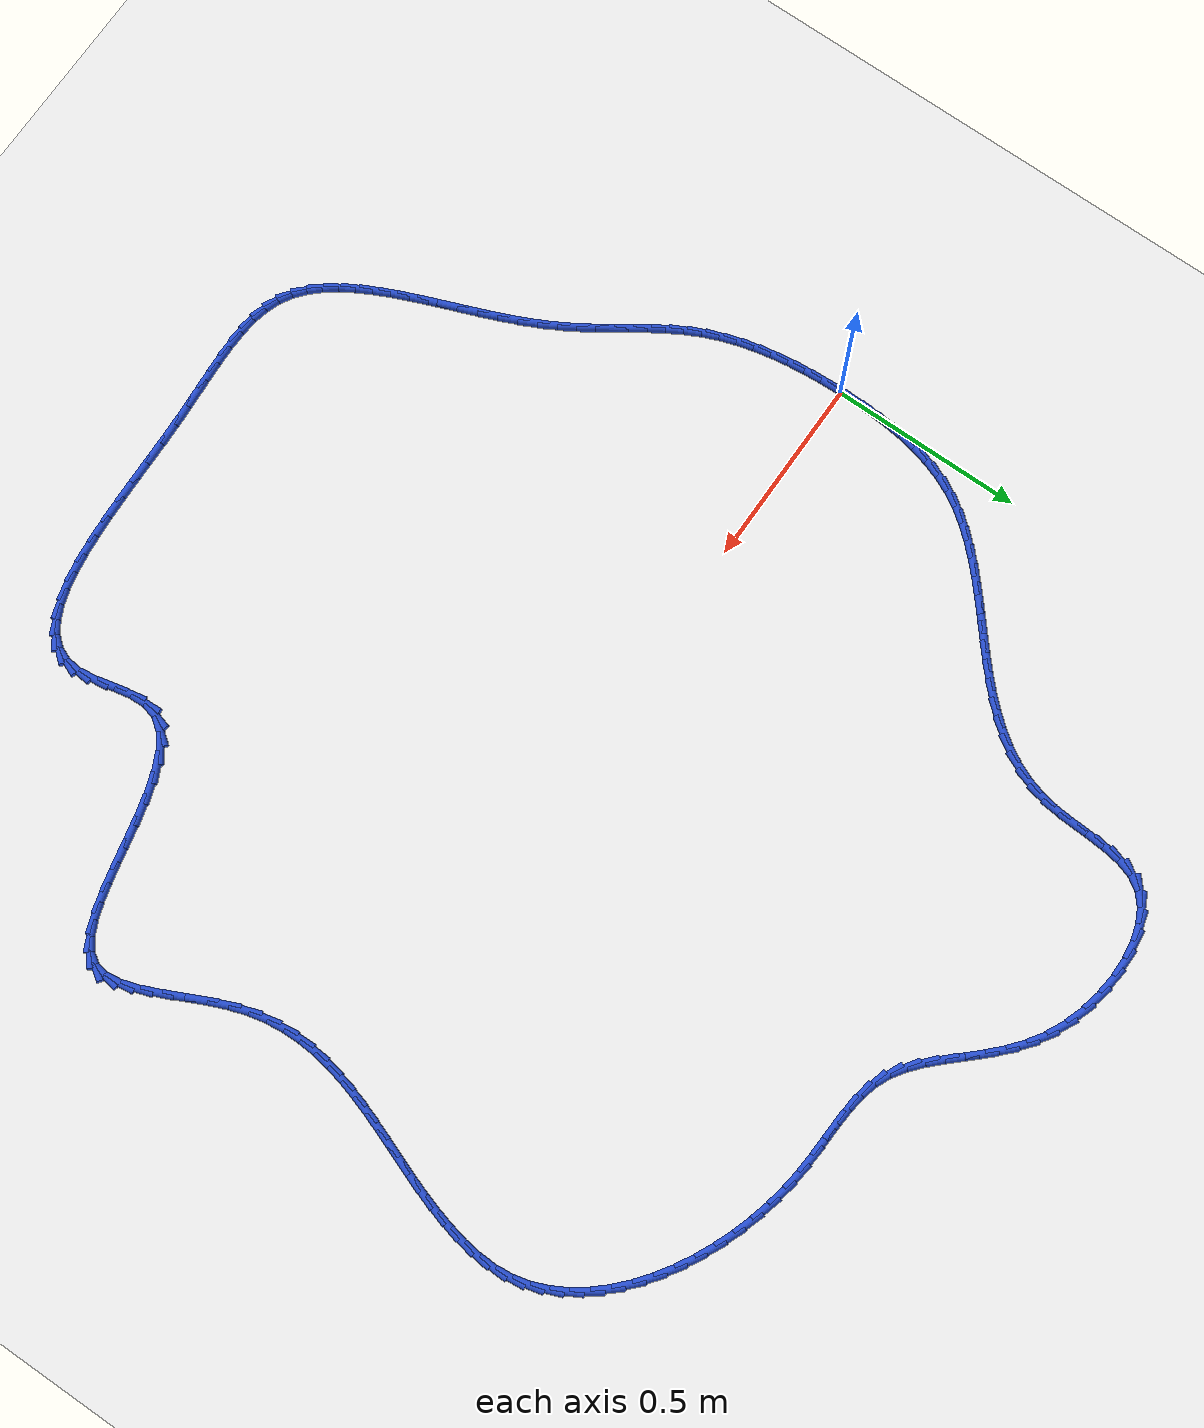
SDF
<sdf version="1.6">
 <world name="default">
  <light name="sun" type="directional">
   <pose>0 0 10 0 -0 0</pose>
   <diffuse>0.8 0.8 0.8 1</diffuse>
   <specular>0.2 0.2 0.2 1</specular>
   <attenuation>
    <range>1000</range>
    <constant>0.9</constant>
    <linear>0.01</linear>
    <quadratic>0.001</quadratic>
   </attenuation>
   <direction>-0.5 0.1 -0.9</direction>
  </light>
  <model name="ground_plane">
   <static>1</static>
   <link name="link">
    <collision name="collision">
     <geometry><plane><normal>0 0 1</normal><size>100 100</size></plane></geometry>
     <surface><friction><ode><mu>100</mu><mu2>50</mu2></ode></friction></surface>
    </collision>
    <visual name="visual">
     <cast_shadows>0</cast_shadows>
     <geometry><plane><normal>0 0 1</normal><size>100 100</size></plane></geometry>
     <material>
      <script><uri>file://media/materials/scripts/gazebo.material</uri><name>Gazebo/WhiteGlow</name></script>
     </material>
    </visual>
   </link>
  </model>
  <gravity>0 0 -9.8</gravity>
  <magnetic_field>6e-06 2.3e-05 -4.2e-05</magnetic_field>
  <atmosphere type="adiabatic"/>
  <physics name="default_physics" default="0" type="ode">
   <max_step_size>0.001</max_step_size>
   <real_time_factor>1</real_time_factor>
   <real_time_update_rate>1000</real_time_update_rate>
  </physics>
  <scene><ambient>0.4 0.4 0.4 1</ambient><background>0.7 0.7 0.7 1</background><shadows>1</shadows></scene>
  <spherical_coordinates>
   <surface_model>EARTH_WGS84</surface_model>
   <latitude_deg>0</latitude_deg>
   <longitude_deg>0</longitude_deg>
   <elevation>0</elevation>
   <heading_deg>0</heading_deg>
  </spherical_coordinates>
  <model name="line">
   <link name="link_0">
    <pose>-6.938893903907228e-18 1.1102230246251565e-16 0.01 0 1.57 -1.5698272240018842</pose>
    <collision name="collision">
     <geometry><cylinder><radius>0.01</radius><length>0.08</length></cylinder></geometry>
    </collision>
    <visual name="visual">
     <material>
      <script><name>Gazebo/Blue</name><uri>file://media/materials/scripts/gazebo.material</uri></script>
     </material>
     <geometry><cylinder><radius>0.01</radius><length>0.08</length></cylinder></geometry>
    </visual>
   </link>
   <link name="link_1">
    <pose>-4.6224713853509084e-05 0.04769844821003116 0.01 0 1.57 1.5362279938505008</pose>
    <collision name="collision">
     <geometry><cylinder><radius>0.01</radius><length>0.08</length></cylinder></geometry>
    </collision>
    <visual name="visual">
     <material>
      <script><name>Gazebo/Blue</name><uri>file://media/materials/scripts/gazebo.material</uri></script>
     </material>
     <geometry><cylinder><radius>0.01</radius><length>0.08</length></cylinder></geometry>
    </visual>
   </link>
   <link name="link_2">
    <pose>0.0015978520212375734 0.09523969966779892 0.01 0 1.57 1.4924991982904947</pose>
    <collision name="collision">
     <geometry><cylinder><radius>0.01</radius><length>0.08</length></cylinder></geometry>
    </collision>
    <visual name="visual">
     <material>
      <script><name>Gazebo/Blue</name><uri>file://media/materials/scripts/gazebo.material</uri></script>
     </material>
     <geometry><cylinder><radius>0.01</radius><length>0.08</length></cylinder></geometry>
    </visual>
   </link>
   <link name="link_3">
    <pose>0.00529207738342137 0.14232537534292586 0.01 0 1.57 1.4398004333818892</pose>
    <collision name="collision">
     <geometry><cylinder><radius>0.01</radius><length>0.08</length></cylinder></geometry>
    </collision>
    <visual name="visual">
     <material>
      <script><name>Gazebo/Blue</name><uri>file://media/materials/scripts/gazebo.material</uri></script>
     </material>
     <geometry><cylinder><radius>0.01</radius><length>0.08</length></cylinder></geometry>
    </visual>
   </link>
   <link name="link_4">
    <pose>0.011396298550846005 0.1886570962050344 0.01 0 1.57 1.3772646589824638</pose>
    <collision name="collision">
     <geometry><cylinder><radius>0.01</radius><length>0.08</length></cylinder></geometry>
    </collision>
    <visual name="visual">
     <material>
      <script><name>Gazebo/Blue</name><uri>file://media/materials/scripts/gazebo.material</uri></script>
     </material>
     <geometry><cylinder><radius>0.01</radius><length>0.08</length></cylinder></geometry>
    </visual>
   </link>
   <link name="link_5">
    <pose>0.020270362701659616 0.23393648322374697 0.01 0 1.57 1.304052633067474</pose>
    <collision name="collision">
     <geometry><cylinder><radius>0.01</radius><length>0.08</length></cylinder></geometry>
    </collision>
    <visual name="visual">
     <material>
      <script><name>Gazebo/Blue</name><uri>file://media/materials/scripts/gazebo.material</uri></script>
     </material>
     <geometry><cylinder><radius>0.01</radius><length>0.08</length></cylinder></geometry>
    </visual>
   </link>
   <link name="link_6">
    <pose>0.032274117014010326 0.27786515736868606 0.01 0 1.57 1.2195438127848641</pose>
    <collision name="collision">
     <geometry><cylinder><radius>0.01</radius><length>0.08</length></cylinder></geometry>
    </collision>
    <visual name="visual">
     <material>
      <script><name>Gazebo/Blue</name><uri>file://media/materials/scripts/gazebo.material</uri></script>
     </material>
     <geometry><cylinder><radius>0.01</radius><length>0.08</length></cylinder></geometry>
    </visual>
   </link>
   <link name="link_7">
    <pose>0.04776740866604626 0.32014473960947404 0.01 0 1.57 1.1236136834559944</pose>
    <collision name="collision">
     <geometry><cylinder><radius>0.01</radius><length>0.08</length></cylinder></geometry>
    </collision>
    <visual name="visual">
     <material>
      <script><name>Gazebo/Blue</name><uri>file://media/materials/scripts/gazebo.material</uri></script>
     </material>
     <geometry><cylinder><radius>0.01</radius><length>0.08</length></cylinder></geometry>
    </visual>
   </link>
   <link name="link_8">
    <pose>0.06711008483591555 0.3604768509157334 0.01 0 1.57 1.0208637279485628</pose>
    <collision name="collision">
     <geometry><cylinder><radius>0.01</radius><length>0.08</length></cylinder></geometry>
    </collision>
    <visual name="visual">
     <material>
      <script><name>Gazebo/Blue</name><uri>file://media/materials/scripts/gazebo.material</uri></script>
     </material>
     <geometry><cylinder><radius>0.01</radius><length>0.08</length></cylinder></geometry>
    </visual>
   </link>
   <link name="link_9">
    <pose>0.09051583271065346 0.3986583702780393 0.01 0 1.57 0.9292621860353677</pose>
    <collision name="collision">
     <geometry><cylinder><radius>0.01</radius><length>0.08</length></cylinder></geometry>
    </collision>
    <visual name="visual">
     <material>
      <script><name>Gazebo/Blue</name><uri>file://media/materials/scripts/gazebo.material</uri></script>
     </material>
     <geometry><cylinder><radius>0.01</radius><length>0.08</length></cylinder></geometry>
    </visual>
   </link>
   <link name="link_10">
    <pose>0.11757848440501183 0.4348901597948855 0.01 0 1.57 0.853887762720206</pose>
    <collision name="collision">
     <geometry><cylinder><radius>0.01</radius><length>0.08</length></cylinder></geometry>
    </collision>
    <visual name="visual">
     <material>
      <script><name>Gazebo/Blue</name><uri>file://media/materials/scripts/gazebo.material</uri></script>
     </material>
     <geometry><cylinder><radius>0.01</radius><length>0.08</length></cylinder></geometry>
    </visual>
   </link>
   <link name="link_11">
    <pose>0.1477275806050789 0.46948015653264685 0.01 0 1.57 0.7943641029480094</pose>
    <collision name="collision">
     <geometry><cylinder><radius>0.01</radius><length>0.08</length></cylinder></geometry>
    </collision>
    <visual name="visual">
     <material>
      <script><name>Gazebo/Blue</name><uri>file://media/materials/scripts/gazebo.material</uri></script>
     </material>
     <geometry><cylinder><radius>0.01</radius><length>0.08</length></cylinder></geometry>
    </visual>
   </link>
   <link name="link_12">
    <pose>0.18039266084863775 0.5027362983060931 0.01 0 1.57 0.749800554762584</pose>
    <collision name="collision">
     <geometry><cylinder><radius>0.01</radius><length>0.08</length></cylinder></geometry>
    </collision>
    <visual name="visual">
     <material>
      <script><name>Gazebo/Blue</name><uri>file://media/materials/scripts/gazebo.material</uri></script>
     </material>
     <geometry><cylinder><radius>0.01</radius><length>0.08</length></cylinder></geometry>
    </visual>
   </link>
   <link name="link_13">
    <pose>0.21500326467347164 0.5349665229299937 0.01 0 1.57 0.719219979925705</pose>
    <collision name="collision">
     <geometry><cylinder><radius>0.01</radius><length>0.08</length></cylinder></geometry>
    </collision>
    <visual name="visual">
     <material>
      <script><name>Gazebo/Blue</name><uri>file://media/materials/scripts/gazebo.material</uri></script>
     </material>
     <geometry><cylinder><radius>0.01</radius><length>0.08</length></cylinder></geometry>
    </visual>
   </link>
   <link name="link_14">
    <pose>0.25098893161736335 0.5664787682191179 0.01 0 1.57 0.7018128583905135</pose>
    <collision name="collision">
     <geometry><cylinder><radius>0.01</radius><length>0.08</length></cylinder></geometry>
    </collision>
    <visual name="visual">
     <material>
      <script><name>Gazebo/Blue</name><uri>file://media/materials/scripts/gazebo.material</uri></script>
     </material>
     <geometry><cylinder><radius>0.01</radius><length>0.08</length></cylinder></geometry>
    </visual>
   </link>
   <link name="link_15">
    <pose>0.2877792012180962 0.597580971988235 0.01 0 1.57 0.6970677124238571</pose>
    <collision name="collision">
     <geometry><cylinder><radius>0.01</radius><length>0.08</length></cylinder></geometry>
    </collision>
    <visual name="visual">
     <material>
      <script><name>Gazebo/Blue</name><uri>file://media/materials/scripts/gazebo.material</uri></script>
     </material>
     <geometry><cylinder><radius>0.01</radius><length>0.08</length></cylinder></geometry>
    </visual>
   </link>
   <link name="link_16">
    <pose>0.3248036130134533 0.6285810720521144 0.01 0 1.57 0.7048271385815194</pose>
    <collision name="collision">
     <geometry><cylinder><radius>0.01</radius><length>0.08</length></cylinder></geometry>
    </collision>
    <visual name="visual">
     <material>
      <script><name>Gazebo/Blue</name><uri>file://media/materials/scripts/gazebo.material</uri></script>
     </material>
     <geometry><cylinder><radius>0.01</radius><length>0.08</length></cylinder></geometry>
    </visual>
   </link>
   <link name="link_17">
    <pose>0.36149170654121765 0.6597870062255258 0.01 0 1.57 0.7252995529724084</pose>
    <collision name="collision">
     <geometry><cylinder><radius>0.01</radius><length>0.08</length></cylinder></geometry>
    </collision>
    <visual name="visual">
     <material>
      <script><name>Gazebo/Blue</name><uri>file://media/materials/scripts/gazebo.material</uri></script>
     </material>
     <geometry><cylinder><radius>0.01</radius><length>0.08</length></cylinder></geometry>
    </visual>
   </link>
   <link name="link_18">
    <pose>0.3972730213391723 0.6915067123232381 0.01 0 1.57 0.7590351079931867</pose>
    <collision name="collision">
     <geometry><cylinder><radius>0.01</radius><length>0.08</length></cylinder></geometry>
    </collision>
    <visual name="visual">
     <material>
      <script><name>Gazebo/Blue</name><uri>file://media/materials/scripts/gazebo.material</uri></script>
     </material>
     <geometry><cylinder><radius>0.01</radius><length>0.08</length></cylinder></geometry>
    </visual>
   </link>
   <link name="link_19">
    <pose>0.4315770969451005 0.7240481281600207 0.01 0 1.57 0.80685312022609</pose>
    <collision name="collision">
     <geometry><cylinder><radius>0.01</radius><length>0.08</length></cylinder></geometry>
    </collision>
    <visual name="visual">
     <material>
      <script><name>Gazebo/Blue</name><uri>file://media/materials/scripts/gazebo.material</uri></script>
     </material>
     <geometry><cylinder><radius>0.01</radius><length>0.08</length></cylinder></geometry>
    </visual>
   </link>
   <link name="link_20">
    <pose>0.46383347289678517 0.7577191915506433 0.01 0 1.57 0.869687519558874</pose>
    <collision name="collision">
     <geometry><cylinder><radius>0.01</radius><length>0.08</length></cylinder></geometry>
    </collision>
    <visual name="visual">
     <material>
      <script><name>Gazebo/Blue</name><uri>file://media/materials/scripts/gazebo.material</uri></script>
     </material>
     <geometry><cylinder><radius>0.01</radius><length>0.08</length></cylinder></geometry>
    </visual>
   </link>
   <link name="link_21">
    <pose>0.4934716887320097 0.7928278403098753 0.01 0 1.57 0.9483012114583834</pose>
    <collision name="collision">
     <geometry><cylinder><radius>0.01</radius><length>0.08</length></cylinder></geometry>
    </collision>
    <visual name="visual">
     <material>
      <script><name>Gazebo/Blue</name><uri>file://media/materials/scripts/gazebo.material</uri></script>
     </material>
     <geometry><cylinder><radius>0.01</radius><length>0.08</length></cylinder></geometry>
    </visual>
   </link>
   <link name="link_22">
    <pose>0.5199212839885567 0.8296820122524855 0.01 0 1.57 1.0428293696407007</pose>
    <collision name="collision">
     <geometry><cylinder><radius>0.01</radius><length>0.08</length></cylinder></geometry>
    </collision>
    <visual name="visual">
     <material>
      <script><name>Gazebo/Blue</name><uri>file://media/materials/scripts/gazebo.material</uri></script>
     </material>
     <geometry><cylinder><radius>0.01</radius><length>0.08</length></cylinder></geometry>
    </visual>
   </link>
   <link name="link_23">
    <pose>0.5426117982042098 0.868589645193244 0.01 0 1.57 1.1521839529303963</pose>
    <collision name="collision">
     <geometry><cylinder><radius>0.01</radius><length>0.08</length></cylinder></geometry>
    </collision>
    <visual name="visual">
     <material>
      <script><name>Gazebo/Blue</name><uri>file://media/materials/scripts/gazebo.material</uri></script>
     </material>
     <geometry><cylinder><radius>0.01</radius><length>0.08</length></cylinder></geometry>
    </visual>
   </link>
   <link name="link_24">
    <pose>0.5609727709167517 0.9098586769469199 0.01 0 1.57 1.2735146775960053</pose>
    <collision name="collision">
     <geometry><cylinder><radius>0.01</radius><length>0.08</length></cylinder></geometry>
    </collision>
    <visual name="visual">
     <material>
      <script><name>Gazebo/Blue</name><uri>file://media/materials/scripts/gazebo.material</uri></script>
     </material>
     <geometry><cylinder><radius>0.01</radius><length>0.08</length></cylinder></geometry>
    </visual>
   </link>
   <link name="link_25">
    <pose>0.5744337416639655 0.9537970453282822 0.01 0 1.57 1.399123777871416</pose>
    <collision name="collision">
     <geometry><cylinder><radius>0.01</radius><length>0.08</length></cylinder></geometry>
    </collision>
    <visual name="visual">
     <material>
      <script><name>Gazebo/Blue</name><uri>file://media/materials/scripts/gazebo.material</uri></script>
     </material>
     <geometry><cylinder><radius>0.01</radius><length>0.08</length></cylinder></geometry>
    </visual>
   </link>
   <link name="link_26">
    <pose>0.5825535647322827 1.0006297990888597 0.01 0 1.57 1.4876768465374621</pose>
    <collision name="collision">
     <geometry><cylinder><radius>0.01</radius><length>0.08</length></cylinder></geometry>
    </collision>
    <visual name="visual">
     <material>
      <script><name>Gazebo/Blue</name><uri>file://media/materials/scripts/gazebo.material</uri></script>
     </material>
     <geometry><cylinder><radius>0.01</radius><length>0.08</length></cylinder></geometry>
    </visual>
   </link>
   <link name="link_27">
    <pose>0.5866226834535703 1.0494720610405956 0.01 0 1.57 1.5190893224431121</pose>
    <collision name="collision">
     <geometry><cylinder><radius>0.01</radius><length>0.08</length></cylinder></geometry>
    </collision>
    <visual name="visual">
     <material>
      <script><name>Gazebo/Blue</name><uri>file://media/materials/scripts/gazebo.material</uri></script>
     </material>
     <geometry><cylinder><radius>0.01</radius><length>0.08</length></cylinder></geometry>
    </visual>
   </link>
   <link name="link_28">
    <pose>0.5891676222018837 1.0986466422077348 0.01 0 1.57 1.4961859262225696</pose>
    <collision name="collision">
     <geometry><cylinder><radius>0.01</radius><length>0.08</length></cylinder></geometry>
    </collision>
    <visual name="visual">
     <material>
      <script><name>Gazebo/Blue</name><uri>file://media/materials/scripts/gazebo.material</uri></script>
     </material>
     <geometry><cylinder><radius>0.01</radius><length>0.08</length></cylinder></geometry>
    </visual>
   </link>
   <link name="link_29">
    <pose>0.5927415748627202 1.1464592588063602 0.01 0 1.57 1.412246910299355</pose>
    <collision name="collision">
     <geometry><cylinder><radius>0.01</radius><length>0.08</length></cylinder></geometry>
    </collision>
    <visual name="visual">
     <material>
      <script><name>Gazebo/Blue</name><uri>file://media/materials/scripts/gazebo.material</uri></script>
     </material>
     <geometry><cylinder><radius>0.01</radius><length>0.08</length></cylinder></geometry>
    </visual>
   </link>
   <link name="link_30">
    <pose>0.5998977353215759 1.1912156270525531 0.01 0 1.57 1.2500295737251466</pose>
    <collision name="collision">
     <geometry><cylinder><radius>0.01</radius><length>0.08</length></cylinder></geometry>
    </collision>
    <visual name="visual">
     <material>
      <script><name>Gazebo/Blue</name><uri>file://media/materials/scripts/gazebo.material</uri></script>
     </material>
     <geometry><cylinder><radius>0.01</radius><length>0.08</length></cylinder></geometry>
    </visual>
   </link>
   <link name="link_31">
    <pose>0.613189297463948 1.2312214631623983 0.01 0 1.57 0.9923208631483486</pose>
    <collision name="collision">
     <geometry><cylinder><radius>0.01</radius><length>0.08</length></cylinder></geometry>
    </collision>
    <visual name="visual">
     <material>
      <script><name>Gazebo/Blue</name><uri>file://media/materials/scripts/gazebo.material</uri></script>
     </material>
     <geometry><cylinder><radius>0.01</radius><length>0.08</length></cylinder></geometry>
    </visual>
   </link>
   <link name="link_32">
    <pose>0.6351193274664706 1.2648053977375362 0.01 0 1.57 0.6994603263338488</pose>
    <collision name="collision">
     <geometry><cylinder><radius>0.01</radius><length>0.08</length></cylinder></geometry>
    </collision>
    <visual name="visual">
     <material>
      <script><name>Gazebo/Blue</name><uri>file://media/materials/scripts/gazebo.material</uri></script>
     </material>
     <geometry><cylinder><radius>0.01</radius><length>0.08</length></cylinder></geometry>
    </visual>
   </link>
   <link name="link_33">
    <pose>0.6663929255618745 1.2911179478330757 0.01 0 1.57 0.45719662307322917</pose>
    <collision name="collision">
     <geometry><cylinder><radius>0.01</radius><length>0.08</length></cylinder></geometry>
    </collision>
    <visual name="visual">
     <material>
      <script><name>Gazebo/Blue</name><uri>file://media/materials/scripts/gazebo.material</uri></script>
     </material>
     <geometry><cylinder><radius>0.01</radius><length>0.08</length></cylinder></geometry>
    </visual>
   </link>
   <link name="link_34">
    <pose>0.7054632210765232 1.3103390517719913 0.01 0 1.57 0.26735341154939035</pose>
    <collision name="collision">
     <geometry><cylinder><radius>0.01</radius><length>0.08</length></cylinder></geometry>
    </collision>
    <visual name="visual">
     <material>
      <script><name>Gazebo/Blue</name><uri>file://media/materials/scripts/gazebo.material</uri></script>
     </material>
     <geometry><cylinder><radius>0.01</radius><length>0.08</length></cylinder></geometry>
    </visual>
   </link>
   <link name="link_35">
    <pose>0.7506409692842806 1.3227137299248182 0.01 0 1.57 0.11588456945361524</pose>
    <collision name="collision">
     <geometry><cylinder><radius>0.01</radius><length>0.08</length></cylinder></geometry>
    </collision>
    <visual name="visual">
     <material>
      <script><name>Gazebo/Blue</name><uri>file://media/materials/scripts/gazebo.material</uri></script>
     </material>
     <geometry><cylinder><radius>0.01</radius><length>0.08</length></cylinder></geometry>
    </visual>
   </link>
   <link name="link_36">
    <pose>0.8002369254590119 1.3284870026620923 0.01 0 1.57 -0.011143603795526572</pose>
    <collision name="collision">
     <geometry><cylinder><radius>0.01</radius><length>0.08</length></cylinder></geometry>
    </collision>
    <visual name="visual">
     <material>
      <script><name>Gazebo/Blue</name><uri>file://media/materials/scripts/gazebo.material</uri></script>
     </material>
     <geometry><cylinder><radius>0.01</radius><length>0.08</length></cylinder></geometry>
    </visual>
   </link>
   <link name="link_37">
    <pose>0.8525618448745811 1.3279038903543487 0.01 0 1.57 -0.12479589124735478</pose>
    <collision name="collision">
     <geometry><cylinder><radius>0.01</radius><length>0.08</length></cylinder></geometry>
    </collision>
    <visual name="visual">
     <material>
      <script><name>Gazebo/Blue</name><uri>file://media/materials/scripts/gazebo.material</uri></script>
     </material>
     <geometry><cylinder><radius>0.01</radius><length>0.08</length></cylinder></geometry>
    </visual>
   </link>
   <link name="link_38">
    <pose>0.9059264828048526 1.3212094133721228 0.01 0 1.57 -0.23391559043876023</pose>
    <collision name="collision">
     <geometry><cylinder><radius>0.01</radius><length>0.08</length></cylinder></geometry>
    </collision>
    <visual name="visual">
     <material>
      <script><name>Gazebo/Blue</name><uri>file://media/materials/scripts/gazebo.material</uri></script>
     </material>
     <geometry><cylinder><radius>0.01</radius><length>0.08</length></cylinder></geometry>
    </visual>
   </link>
   <link name="link_39">
    <pose>0.958641594523691 1.3086485920859499 0.01 0 1.57 -0.3463753444541136</pose>
    <collision name="collision">
     <geometry><cylinder><radius>0.01</radius><length>0.08</length></cylinder></geometry>
    </collision>
    <visual name="visual">
     <material>
      <script><name>Gazebo/Blue</name><uri>file://media/materials/scripts/gazebo.material</uri></script>
     </material>
     <geometry><cylinder><radius>0.01</radius><length>0.08</length></cylinder></geometry>
    </visual>
   </link>
   <link name="link_40">
    <pose>1.0090179353049606 1.2904664468663654 0.01 0 1.57 -0.47014789101066307</pose>
    <collision name="collision">
     <geometry><cylinder><radius>0.01</radius><length>0.08</length></cylinder></geometry>
    </collision>
    <visual name="visual">
     <material>
      <script><name>Gazebo/Blue</name><uri>file://media/materials/scripts/gazebo.material</uri></script>
     </material>
     <geometry><cylinder><radius>0.01</radius><length>0.08</length></cylinder></geometry>
    </visual>
   </link>
   <link name="link_41">
    <pose>1.055373129990146 1.2669109637216691 0.01 0 1.57 -0.5987343801595141</pose>
    <collision name="collision">
     <geometry><cylinder><radius>0.01</radius><length>0.08</length></cylinder></geometry>
    </collision>
    <visual name="visual">
     <material>
      <script><name>Gazebo/Blue</name><uri>file://media/materials/scripts/gazebo.material</uri></script>
     </material>
     <geometry><cylinder><radius>0.01</radius><length>0.08</length></cylinder></geometry>
    </visual>
   </link>
   <link name="link_42">
    <pose>1.0968731021812408 1.2385963448442086 0.01 0 1.57 -0.7028953255629611</pose>
    <collision name="collision">
     <geometry><cylinder><radius>0.01</radius><length>0.08</length></cylinder></geometry>
    </collision>
    <visual name="visual">
     <material>
      <script><name>Gazebo/Blue</name><uri>file://media/materials/scripts/gazebo.material</uri></script>
     </material>
     <geometry><cylinder><radius>0.01</radius><length>0.08</length></cylinder></geometry>
    </visual>
   </link>
   <link name="link_43">
    <pose>1.1343405657984749 1.2068520397617704 0.01 0 1.57 -0.7753192075446043</pose>
    <collision name="collision">
     <geometry><cylinder><radius>0.01</radius><length>0.08</length></cylinder></geometry>
    </collision>
    <visual name="visual">
     <material>
      <script><name>Gazebo/Blue</name><uri>file://media/materials/scripts/gazebo.material</uri></script>
     </material>
     <geometry><cylinder><radius>0.01</radius><length>0.08</length></cylinder></geometry>
    </visual>
   </link>
   <link name="link_44">
    <pose>1.168789889259764 1.1730902365160525 0.01 0 1.57 -0.814150677451299</pose>
    <collision name="collision">
     <geometry><cylinder><radius>0.01</radius><length>0.08</length></cylinder></geometry>
    </collision>
    <visual name="visual">
     <material>
      <script><name>Gazebo/Blue</name><uri>file://media/materials/scripts/gazebo.material</uri></script>
     </material>
     <geometry><cylinder><radius>0.01</radius><length>0.08</length></cylinder></geometry>
    </visual>
   </link>
   <link name="link_45">
    <pose>1.2012354409830235 1.1387231231487531 0.01 0 1.57 -0.817749285158957</pose>
    <collision name="collision">
     <geometry><cylinder><radius>0.01</radius><length>0.08</length></cylinder></geometry>
    </collision>
    <visual name="visual">
     <material>
      <script><name>Gazebo/Blue</name><uri>file://media/materials/scripts/gazebo.material</uri></script>
     </material>
     <geometry><cylinder><radius>0.01</radius><length>0.08</length></cylinder></geometry>
    </visual>
   </link>
   <link name="link_46">
    <pose>1.2326915893861674 1.1051628877015707 0.01 0 1.57 -0.7831705496043173</pose>
    <collision name="collision">
     <geometry><cylinder><radius>0.01</radius><length>0.08</length></cylinder></geometry>
    </collision>
    <visual name="visual">
     <material>
      <script><name>Gazebo/Blue</name><uri>file://media/materials/scripts/gazebo.material</uri></script>
     </material>
     <geometry><cylinder><radius>0.01</radius><length>0.08</length></cylinder></geometry>
    </visual>
   </link>
   <link name="link_47">
    <pose>1.2641727028871113 1.0738217182162029 0.01 0 1.57 -0.705698466199918</pose>
    <collision name="collision">
     <geometry><cylinder><radius>0.01</radius><length>0.08</length></cylinder></geometry>
    </collision>
    <visual name="visual">
     <material>
      <script><name>Gazebo/Blue</name><uri>file://media/materials/scripts/gazebo.material</uri></script>
     </material>
     <geometry><cylinder><radius>0.01</radius><length>0.08</length></cylinder></geometry>
    </visual>
   </link>
   <link name="link_48">
    <pose>1.2966931499037706 1.046111802734349 0.01 0 1.57 -0.5802950338210349</pose>
    <collision name="collision">
     <geometry><cylinder><radius>0.01</radius><length>0.08</length></cylinder></geometry>
    </collision>
    <visual name="visual">
     <material>
      <script><name>Gazebo/Blue</name><uri>file://media/materials/scripts/gazebo.material</uri></script>
     </material>
     <geometry><cylinder><radius>0.01</radius><length>0.08</length></cylinder></geometry>
    </visual>
   </link>
   <link name="link_49">
    <pose>1.3312672988540595 1.0234453292977066 0.01 0 1.57 -0.40958373161698175</pose>
    <collision name="collision">
     <geometry><cylinder><radius>0.01</radius><length>0.08</length></cylinder></geometry>
    </collision>
    <visual name="visual">
     <material>
      <script><name>Gazebo/Blue</name><uri>file://media/materials/scripts/gazebo.material</uri></script>
     </material>
     <geometry><cylinder><radius>0.01</radius><length>0.08</length></cylinder></geometry>
    </visual>
   </link>
   <link name="link_50">
    <pose>1.3688570420879036 1.007126253837911 0.01 0 1.57 -0.2471009292330219</pose>
    <collision name="collision">
     <geometry><cylinder><radius>0.01</radius><length>0.08</length></cylinder></geometry>
    </collision>
    <visual name="visual">
     <material>
      <script><name>Gazebo/Blue</name><uri>file://media/materials/scripts/gazebo.material</uri></script>
     </material>
     <geometry><cylinder><radius>0.01</radius><length>0.08</length></cylinder></geometry>
    </visual>
   </link>
   <link name="link_51">
    <pose>1.4096389353122558 0.9968387721705373 0.01 0 1.57 -0.132835897227499</pose>
    <collision name="collision">
     <geometry><cylinder><radius>0.01</radius><length>0.08</length></cylinder></geometry>
    </collision>
    <visual name="visual">
     <material>
      <script><name>Gazebo/Blue</name><uri>file://media/materials/scripts/gazebo.material</uri></script>
     </material>
     <geometry><cylinder><radius>0.01</radius><length>0.08</length></cylinder></geometry>
    </visual>
   </link>
   <link name="link_52">
    <pose>1.4531849093393314 0.9910200387328647 0.01 0 1.57 -0.06411837149518201</pose>
    <collision name="collision">
     <geometry><cylinder><radius>0.01</radius><length>0.08</length></cylinder></geometry>
    </collision>
    <visual name="visual">
     <material>
      <script><name>Gazebo/Blue</name><uri>file://media/materials/scripts/gazebo.material</uri></script>
     </material>
     <geometry><cylinder><radius>0.01</radius><length>0.08</length></cylinder></geometry>
    </visual>
   </link>
   <link name="link_53">
    <pose>1.4990513378167134 0.9880751212449503 0.01 0 1.57 -0.034881534755693236</pose>
    <collision name="collision">
     <geometry><cylinder><radius>0.01</radius><length>0.08</length></cylinder></geometry>
    </collision>
    <visual name="visual">
     <material>
      <script><name>Gazebo/Blue</name><uri>file://media/materials/scripts/gazebo.material</uri></script>
     </material>
     <geometry><cylinder><radius>0.01</radius><length>0.08</length></cylinder></geometry>
    </visual>
   </link>
   <link name="link_54">
    <pose>1.5467945943919854 0.9864090874268507 0.01 0 1.57 -0.04028370932859828</pose>
    <collision name="collision">
     <geometry><cylinder><radius>0.01</radius><length>0.08</length></cylinder></geometry>
    </collision>
    <visual name="visual">
     <material>
      <script><name>Gazebo/Blue</name><uri>file://media/materials/scripts/gazebo.material</uri></script>
     </material>
     <geometry><cylinder><radius>0.01</radius><length>0.08</length></cylinder></geometry>
    </visual>
   </link>
   <link name="link_55">
    <pose>1.5959710527127318 0.9844270049986226 0.01 0 1.57 -0.07744834632753267</pose>
    <collision name="collision">
     <geometry><cylinder><radius>0.01</radius><length>0.08</length></cylinder></geometry>
    </collision>
    <visual name="visual">
     <material>
      <script><name>Gazebo/Blue</name><uri>file://media/materials/scripts/gazebo.material</uri></script>
     </material>
     <geometry><cylinder><radius>0.01</radius><length>0.08</length></cylinder></geometry>
    </visual>
   </link>
   <link name="link_56">
    <pose>1.6461370864265352 0.9805339416803227 0.01 0 1.57 -0.13969205797044207</pose>
    <collision name="collision">
     <geometry><cylinder><radius>0.01</radius><length>0.08</length></cylinder></geometry>
    </collision>
    <visual name="visual">
     <material>
      <script><name>Gazebo/Blue</name><uri>file://media/materials/scripts/gazebo.material</uri></script>
     </material>
     <geometry><cylinder><radius>0.01</radius><length>0.08</length></cylinder></geometry>
    </visual>
   </link>
   <link name="link_57">
    <pose>1.696846908103053 0.9734037426210439 0.01 0 1.57 -0.2046522275101746</pose>
    <collision name="collision">
     <geometry><cylinder><radius>0.01</radius><length>0.08</length></cylinder></geometry>
    </collision>
    <visual name="visual">
     <material>
      <script><name>Gazebo/Blue</name><uri>file://media/materials/scripts/gazebo.material</uri></script>
     </material>
     <geometry><cylinder><radius>0.01</radius><length>0.08</length></cylinder></geometry>
    </visual>
   </link>
   <link name="link_58">
    <pose>1.7476454851650143 0.9628600897209857 0.01 0 1.57 -0.2675880855610507</pose>
    <collision name="collision">
     <geometry><cylinder><radius>0.01</radius><length>0.08</length></cylinder></geometry>
    </collision>
    <visual name="visual">
     <material>
      <script><name>Gazebo/Blue</name><uri>file://media/materials/scripts/gazebo.material</uri></script>
     </material>
     <geometry><cylinder><radius>0.01</radius><length>0.08</length></cylinder></geometry>
    </visual>
   </link>
   <link name="link_59">
    <pose>1.7980753132442133 0.9490340862851032 0.01 0 1.57 -0.32976162530008307</pose>
    <collision name="collision">
     <geometry><cylinder><radius>0.01</radius><length>0.08</length></cylinder></geometry>
    </collision>
    <visual name="visual">
     <material>
      <script><name>Gazebo/Blue</name><uri>file://media/materials/scripts/gazebo.material</uri></script>
     </material>
     <geometry><cylinder><radius>0.01</radius><length>0.08</length></cylinder></geometry>
    </visual>
   </link>
   <link name="link_60">
    <pose>1.8476788879464745 0.9320568388484122 0.01 0 1.57 -0.3923927622506366</pose>
    <collision name="collision">
     <geometry><cylinder><radius>0.01</radius><length>0.08</length></cylinder></geometry>
    </collision>
    <visual name="visual">
     <material>
      <script><name>Gazebo/Blue</name><uri>file://media/materials/scripts/gazebo.material</uri></script>
     </material>
     <geometry><cylinder><radius>0.01</radius><length>0.08</length></cylinder></geometry>
    </visual>
   </link>
   <link name="link_61">
    <pose>1.8959987048776235 0.9120594539459299 0.01 0 1.57 -0.4567044370363693</pose>
    <collision name="collision">
     <geometry><cylinder><radius>0.01</radius><length>0.08</length></cylinder></geometry>
    </collision>
    <visual name="visual">
     <material>
      <script><name>Gazebo/Blue</name><uri>file://media/materials/scripts/gazebo.material</uri></script>
     </material>
     <geometry><cylinder><radius>0.01</radius><length>0.08</length></cylinder></geometry>
    </visual>
   </link>
   <link name="link_62">
    <pose>1.9425772596434834 0.8891730381126728 0.01 0 1.57 -0.5239647020566908</pose>
    <collision name="collision">
     <geometry><cylinder><radius>0.01</radius><length>0.08</length></cylinder></geometry>
    </collision>
    <visual name="visual">
     <material>
      <script><name>Gazebo/Blue</name><uri>file://media/materials/scripts/gazebo.material</uri></script>
     </material>
     <geometry><cylinder><radius>0.01</radius><length>0.08</length></cylinder></geometry>
    </visual>
   </link>
   <link name="link_63">
    <pose>1.98695704784988 0.863528697883657 0.01 0 1.57 -0.5955222361642104</pose>
    <collision name="collision">
     <geometry><cylinder><radius>0.01</radius><length>0.08</length></cylinder></geometry>
    </collision>
    <visual name="visual">
     <material>
      <script><name>Gazebo/Blue</name><uri>file://media/materials/scripts/gazebo.material</uri></script>
     </material>
     <geometry><cylinder><radius>0.01</radius><length>0.08</length></cylinder></geometry>
    </visual>
   </link>
   <link name="link_64">
    <pose>2.028680565102636 0.8352575397938995 0.01 0 1.57 -0.6728282916552596</pose>
    <collision name="collision">
     <geometry><cylinder><radius>0.01</radius><length>0.08</length></cylinder></geometry>
    </collision>
    <visual name="visual">
     <material>
      <script><name>Gazebo/Blue</name><uri>file://media/materials/scripts/gazebo.material</uri></script>
     </material>
     <geometry><cylinder><radius>0.01</radius><length>0.08</length></cylinder></geometry>
    </visual>
   </link>
   <link name="link_65">
    <pose>2.067290307007577 0.8044906703784166 0.01 0 1.57 -0.7574314253281289</pose>
    <collision name="collision">
     <geometry><cylinder><radius>0.01</radius><length>0.08</length></cylinder></geometry>
    </collision>
    <visual name="visual">
     <material>
      <script><name>Gazebo/Blue</name><uri>file://media/materials/scripts/gazebo.material</uri></script>
     </material>
     <geometry><cylinder><radius>0.01</radius><length>0.08</length></cylinder></geometry>
    </visual>
   </link>
   <link name="link_66">
    <pose>2.1023287691705272 0.7713591961722244 0.01 0 1.57 -0.8509210675143829</pose>
    <collision name="collision">
     <geometry><cylinder><radius>0.01</radius><length>0.08</length></cylinder></geometry>
    </collision>
    <visual name="visual">
     <material>
      <script><name>Gazebo/Blue</name><uri>file://media/materials/scripts/gazebo.material</uri></script>
     </material>
     <geometry><cylinder><radius>0.01</radius><length>0.08</length></cylinder></geometry>
    </visual>
   </link>
   <link name="link_67">
    <pose>2.1333384471973114 0.7359942237103403 0.01 0 1.57 -0.9547836935951365</pose>
    <collision name="collision">
     <geometry><cylinder><radius>0.01</radius><length>0.08</length></cylinder></geometry>
    </collision>
    <visual name="visual">
     <material>
      <script><name>Gazebo/Blue</name><uri>file://media/materials/scripts/gazebo.material</uri></script>
     </material>
     <geometry><cylinder><radius>0.01</radius><length>0.08</length></cylinder></geometry>
    </visual>
   </link>
   <link name="link_68">
    <pose>2.1598618366937536 0.6985268595277802 0.01 0 1.57 -1.0701294168392044</pose>
    <collision name="collision">
     <geometry><cylinder><radius>0.01</radius><length>0.08</length></cylinder></geometry>
    </collision>
    <visual name="visual">
     <material>
      <script><name>Gazebo/Blue</name><uri>file://media/materials/scripts/gazebo.material</uri></script>
     </material>
     <geometry><cylinder><radius>0.01</radius><length>0.08</length></cylinder></geometry>
    </visual>
   </link>
   <link name="link_69">
    <pose>2.1814414332656784 0.659088210159561 0.01 0 1.57 -1.1972684944772813</pose>
    <collision name="collision">
     <geometry><cylinder><radius>0.01</radius><length>0.08</length></cylinder></geometry>
    </collision>
    <visual name="visual">
     <material>
      <script><name>Gazebo/Blue</name><uri>file://media/materials/scripts/gazebo.material</uri></script>
     </material>
     <geometry><cylinder><radius>0.01</radius><length>0.08</length></cylinder></geometry>
    </visual>
   </link>
   <link name="link_70">
    <pose>2.1976197325189095 0.617809382140699 0.01 0 1.57 -1.335198524556531</pose>
    <collision name="collision">
     <geometry><cylinder><radius>0.01</radius><length>0.08</length></cylinder></geometry>
    </collision>
    <visual name="visual">
     <material>
      <script><name>Gazebo/Blue</name><uri>file://media/materials/scripts/gazebo.material</uri></script>
     </material>
     <geometry><cylinder><radius>0.01</radius><length>0.08</length></cylinder></geometry>
    </visual>
   </link>
   <link name="link_71">
    <pose>2.207939230059273 0.5748214820062107 0.01 0 1.57 -1.4797326259009584</pose>
    <collision name="collision">
     <geometry><cylinder><radius>0.01</radius><length>0.08</length></cylinder></geometry>
    </collision>
    <visual name="visual">
     <material>
      <script><name>Gazebo/Blue</name><uri>file://media/materials/scripts/gazebo.material</uri></script>
     </material>
     <geometry><cylinder><radius>0.01</radius><length>0.08</length></cylinder></geometry>
    </visual>
   </link>
   <link name="link_72">
    <pose>2.2120068470290923 0.5302772014035426 0.01 0 1.57 1.5339025078505513</pose>
    <collision name="collision">
     <geometry><cylinder><radius>0.01</radius><length>0.08</length></cylinder></geometry>
    </collision>
    <visual name="visual">
     <material>
      <script><name>Gazebo/Blue</name><uri>file://media/materials/scripts/gazebo.material</uri></script>
     </material>
     <geometry><cylinder><radius>0.01</radius><length>0.08</length></cylinder></geometry>
    </visual>
   </link>
   <link name="link_73">
    <pose>2.2103219174329536 0.484628225717903 0.01 0 1.57 1.435227888968891</pose>
    <collision name="collision">
     <geometry><cylinder><radius>0.01</radius><length>0.08</length></cylinder></geometry>
    </collision>
    <visual name="visual">
     <material>
      <script><name>Gazebo/Blue</name><uri>file://media/materials/scripts/gazebo.material</uri></script>
     </material>
     <geometry><cylinder><radius>0.01</radius><length>0.08</length></cylinder></geometry>
    </visual>
   </link>
   <link name="link_74">
    <pose>2.204035892144817 0.4385447253748639 0.01 0 1.57 1.3617427327181393</pose>
    <collision name="collision">
     <geometry><cylinder><radius>0.01</radius><length>0.08</length></cylinder></geometry>
    </collision>
    <visual name="visual">
     <material>
      <script><name>Gazebo/Blue</name><uri>file://media/materials/scripts/gazebo.material</uri></script>
     </material>
     <geometry><cylinder><radius>0.01</radius><length>0.08</length></cylinder></geometry>
    </visual>
   </link>
   <link name="link_75">
    <pose>2.1943083415701703 0.39269319632066535 0.01 0 1.57 1.306293230474202</pose>
    <collision name="collision">
     <geometry><cylinder><radius>0.01</radius><length>0.08</length></cylinder></geometry>
    </collision>
    <visual name="visual">
     <material>
      <script><name>Gazebo/Blue</name><uri>file://media/materials/scripts/gazebo.material</uri></script>
     </material>
     <geometry><cylinder><radius>0.01</radius><length>0.08</length></cylinder></geometry>
    </visual>
   </link>
   <link name="link_76">
    <pose>2.1820446405932965 0.34741447920468616 0.01 0 1.57 1.2633309405001432</pose>
    <collision name="collision">
     <geometry><cylinder><radius>0.01</radius><length>0.08</length></cylinder></geometry>
    </collision>
    <visual name="visual">
     <material>
      <script><name>Gazebo/Blue</name><uri>file://media/materials/scripts/gazebo.material</uri></script>
     </material>
     <geometry><cylinder><radius>0.01</radius><length>0.08</length></cylinder></geometry>
    </visual>
   </link>
   <link name="link_77">
    <pose>2.1678248303526586 0.30263262268456276 0.01 0 1.57 1.2324912851083443</pose>
    <collision name="collision">
     <geometry><cylinder><radius>0.01</radius><length>0.08</length></cylinder></geometry>
    </collision>
    <visual name="visual">
     <material>
      <script><name>Gazebo/Blue</name><uri>file://media/materials/scripts/gazebo.material</uri></script>
     </material>
     <geometry><cylinder><radius>0.01</radius><length>0.08</length></cylinder></geometry>
    </visual>
   </link>
   <link name="link_78">
    <pose>2.152207692947173 0.25824444000952995 0.01 0 1.57 1.213636072155509</pose>
    <collision name="collision">
     <geometry><cylinder><radius>0.01</radius><length>0.08</length></cylinder></geometry>
    </collision>
    <visual name="visual">
     <material>
      <script><name>Gazebo/Blue</name><uri>file://media/materials/scripts/gazebo.material</uri></script>
     </material>
     <geometry><cylinder><radius>0.01</radius><length>0.08</length></cylinder></geometry>
    </visual>
   </link>
   <link name="link_79">
    <pose>2.1357520104757546 0.21414674442882006 0.01 0 1.57 1.2066647263229426</pose>
    <collision name="collision">
     <geometry><cylinder><radius>0.01</radius><length>0.08</length></cylinder></geometry>
    </collision>
    <visual name="visual">
     <material>
      <script><name>Gazebo/Blue</name><uri>file://media/materials/scripts/gazebo.material</uri></script>
     </material>
     <geometry><cylinder><radius>0.01</radius><length>0.08</length></cylinder></geometry>
    </visual>
   </link>
   <link name="link_80">
    <pose>2.1190165650373203 0.1702363491916677 0.01 0 1.57 1.2115942206766528</pose>
    <collision name="collision">
     <geometry><cylinder><radius>0.01</radius><length>0.08</length></cylinder></geometry>
    </collision>
    <visual name="visual">
     <material>
      <script><name>Gazebo/Blue</name><uri>file://media/materials/scripts/gazebo.material</uri></script>
     </material>
     <geometry><cylinder><radius>0.01</radius><length>0.08</length></cylinder></geometry>
    </visual>
   </link>
   <link name="link_81">
    <pose>2.1025601387307873 0.126410067547306 0.01 0 1.57 1.2285904234382172</pose>
    <collision name="collision">
     <geometry><cylinder><radius>0.01</radius><length>0.08</length></cylinder></geometry>
    </collision>
    <visual name="visual">
     <material>
      <script><name>Gazebo/Blue</name><uri>file://media/materials/scripts/gazebo.material</uri></script>
     </material>
     <geometry><cylinder><radius>0.01</radius><length>0.08</length></cylinder></geometry>
    </visual>
   </link>
   <link name="link_82">
    <pose>2.0869415136550704 0.08256471274496804 0.01 0 1.57 1.2579522297177779</pose>
    <collision name="collision">
     <geometry><cylinder><radius>0.01</radius><length>0.08</length></cylinder></geometry>
    </collision>
    <visual name="visual">
     <material>
      <script><name>Gazebo/Blue</name><uri>file://media/materials/scripts/gazebo.material</uri></script>
     </material>
     <geometry><cylinder><radius>0.01</radius><length>0.08</length></cylinder></geometry>
    </visual>
   </link>
   <link name="link_83">
    <pose>2.0727194719090867 0.0385970980338883 0.01 0 1.57 1.3000422069692195</pose>
    <collision name="collision">
     <geometry><cylinder><radius>0.01</radius><length>0.08</length></cylinder></geometry>
    </collision>
    <visual name="visual">
     <material>
      <script><name>Gazebo/Blue</name><uri>file://media/materials/scripts/gazebo.material</uri></script>
     </material>
     <geometry><cylinder><radius>0.01</radius><length>0.08</length></cylinder></geometry>
    </visual>
   </link>
   <link name="link_84">
    <pose>2.060452795591752 -0.005595963336700552 0.01 0 1.57 1.3551512401351415</pose>
    <collision name="collision">
     <geometry><cylinder><radius>0.01</radius><length>0.08</length></cylinder></geometry>
    </collision>
    <visual name="visual">
     <material>
      <script><name>Gazebo/Blue</name><uri>file://media/materials/scripts/gazebo.material</uri></script>
     </material>
     <geometry><cylinder><radius>0.01</radius><length>0.08</length></cylinder></geometry>
    </visual>
   </link>
   <link name="link_85">
    <pose>2.0507002668019827 -0.05011765811756408 0.01 0 1.57 1.4232865861265551</pose>
    <collision name="collision">
     <geometry><cylinder><radius>0.01</radius><length>0.08</length></cylinder></geometry>
    </collision>
    <visual name="visual">
     <material>
      <script><name>Gazebo/Blue</name><uri>file://media/materials/scripts/gazebo.material</uri></script>
     </material>
     <geometry><cylinder><radius>0.01</radius><length>0.08</length></cylinder></geometry>
    </visual>
   </link>
   <link name="link_86">
    <pose>2.0440206676386947 -0.09507117305946917 0.01 0 1.57 1.5038928874892956</pose>
    <collision name="collision">
     <geometry><cylinder><radius>0.01</radius><length>0.08</length></cylinder></geometry>
    </collision>
    <visual name="visual">
     <material>
      <script><name>Gazebo/Blue</name><uri>file://media/materials/scripts/gazebo.material</uri></script>
     </material>
     <geometry><cylinder><radius>0.01</radius><length>0.08</length></cylinder></geometry>
    </visual>
   </link>
   <link name="link_87">
    <pose>2.040972780200805 -0.1405596949131822 0.01 0 1.57 -1.546030358591935</pose>
    <collision name="collision">
     <geometry><cylinder><radius>0.01</radius><length>0.08</length></cylinder></geometry>
    </collision>
    <visual name="visual">
     <material>
      <script><name>Gazebo/Blue</name><uri>file://media/materials/scripts/gazebo.material</uri></script>
     </material>
     <geometry><cylinder><radius>0.01</radius><length>0.08</length></cylinder></geometry>
    </visual>
   </link>
   <link name="link_88">
    <pose>2.0421153865872284 -0.18668641042946965 0.01 0 1.57 -1.445740342718742</pose>
    <collision name="collision">
     <geometry><cylinder><radius>0.01</radius><length>0.08</length></cylinder></geometry>
    </collision>
    <visual name="visual">
     <material>
      <script><name>Gazebo/Blue</name><uri>file://media/materials/scripts/gazebo.material</uri></script>
     </material>
     <geometry><cylinder><radius>0.01</radius><length>0.08</length></cylinder></geometry>
    </visual>
   </link>
   <link name="link_89">
    <pose>2.048007268896883 -0.2335545063590989 0.01 0 1.57 -1.3402333599834049</pose>
    <collision name="collision">
     <geometry><cylinder><radius>0.01</radius><length>0.08</length></cylinder></geometry>
    </collision>
    <visual name="visual">
     <material>
      <script><name>Gazebo/Blue</name><uri>file://media/materials/scripts/gazebo.material</uri></script>
     </material>
     <geometry><cylinder><radius>0.01</radius><length>0.08</length></cylinder></geometry>
    </visual>
   </link>
   <link name="link_90">
    <pose>2.059207209228683 -0.2812671694528344 0.01 0 1.57 -1.2361242878296406</pose>
    <collision name="collision">
     <geometry><cylinder><radius>0.01</radius><length>0.08</length></cylinder></geometry>
    </collision>
    <visual name="visual">
     <material>
      <script><name>Gazebo/Blue</name><uri>file://media/materials/scripts/gazebo.material</uri></script>
     </material>
     <geometry><cylinder><radius>0.01</radius><length>0.08</length></cylinder></geometry>
    </visual>
   </link>
   <link name="link_91">
    <pose>2.0761110477318416 -0.3298758560582445 0.01 0 1.57 -1.162174759735885</pose>
    <collision name="collision">
     <geometry><cylinder><radius>0.01</radius><length>0.08</length></cylinder></geometry>
    </collision>
    <visual name="visual">
     <material>
      <script><name>Gazebo/Blue</name><uri>file://media/materials/scripts/gazebo.material</uri></script>
     </material>
     <geometry><cylinder><radius>0.01</radius><length>0.08</length></cylinder></geometry>
    </visual>
   </link>
   <link name="link_92">
    <pose>2.097322132698221 -0.37886294668527154 0.01 0 1.57 -1.127745093713557</pose>
    <collision name="collision">
     <geometry><cylinder><radius>0.01</radius><length>0.08</length></cylinder></geometry>
    </collision>
    <visual name="visual">
     <material>
      <script><name>Gazebo/Blue</name><uri>file://media/materials/scripts/gazebo.material</uri></script>
     </material>
     <geometry><cylinder><radius>0.01</radius><length>0.08</length></cylinder></geometry>
    </visual>
   </link>
   <link name="link_93">
    <pose>2.1203338979892616 -0.4273584489828084 0.01 0 1.57 -1.129024447233397</pose>
    <collision name="collision">
     <geometry><cylinder><radius>0.01</radius><length>0.08</length></cylinder></geometry>
    </collision>
    <visual name="visual">
     <material>
      <script><name>Gazebo/Blue</name><uri>file://media/materials/scripts/gazebo.material</uri></script>
     </material>
     <geometry><cylinder><radius>0.01</radius><length>0.08</length></cylinder></geometry>
    </visual>
   </link>
   <link name="link_94">
    <pose>2.142623261422383 -0.4744871271273454 0.01 0 1.57 -1.1695472942777323</pose>
    <collision name="collision">
     <geometry><cylinder><radius>0.01</radius><length>0.08</length></cylinder></geometry>
    </collision>
    <visual name="visual">
     <material>
      <script><name>Gazebo/Blue</name><uri>file://media/materials/scripts/gazebo.material</uri></script>
     </material>
     <geometry><cylinder><radius>0.01</radius><length>0.08</length></cylinder></geometry>
    </visual>
   </link>
   <link name="link_95">
    <pose>2.161667140815 -0.5193737452953698 0.01 0 1.57 -1.2630680662964158</pose>
    <collision name="collision">
     <geometry><cylinder><radius>0.01</radius><length>0.08</length></cylinder></geometry>
    </collision>
    <visual name="visual">
     <material>
      <script><name>Gazebo/Blue</name><uri>file://media/materials/scripts/gazebo.material</uri></script>
     </material>
     <geometry><cylinder><radius>0.01</radius><length>0.08</length></cylinder></geometry>
    </visual>
   </link>
   <link name="link_96">
    <pose>2.1749424539845306 -0.5611430676633719 0.01 0 1.57 -1.4396297805224285</pose>
    <collision name="collision">
     <geometry><cylinder><radius>0.01</radius><length>0.08</length></cylinder></geometry>
    </collision>
    <visual name="visual">
     <material>
      <script><name>Gazebo/Blue</name><uri>file://media/materials/scripts/gazebo.material</uri></script>
     </material>
     <geometry><cylinder><radius>0.01</radius><length>0.08</length></cylinder></geometry>
    </visual>
   </link>
   <link name="link_97">
    <pose>2.179926118748391 -0.5989198584078407 0.01 0 1.57 1.395429004421171</pose>
    <collision name="collision">
     <geometry><cylinder><radius>0.01</radius><length>0.08</length></cylinder></geometry>
    </collision>
    <visual name="visual">
     <material>
      <script><name>Gazebo/Blue</name><uri>file://media/materials/scripts/gazebo.material</uri></script>
     </material>
     <geometry><cylinder><radius>0.01</radius><length>0.08</length></cylinder></geometry>
    </visual>
   </link>
   <link name="link_98">
    <pose>2.174095052923999 -0.6318288817052654 0.01 0 1.57 0.97766791986823</pose>
    <collision name="collision">
     <geometry><cylinder><radius>0.01</radius><length>0.08</length></cylinder></geometry>
    </collision>
    <visual name="visual">
     <material>
      <script><name>Gazebo/Blue</name><uri>file://media/materials/scripts/gazebo.material</uri></script>
     </material>
     <geometry><cylinder><radius>0.01</radius><length>0.08</length></cylinder></geometry>
    </visual>
   </link>
   <link name="link_99">
    <pose>2.1556006908460525 -0.6592646779352935 0.01 0 1.57 0.645076575240495</pose>
    <collision name="collision">
     <geometry><cylinder><radius>0.01</radius><length>0.08</length></cylinder></geometry>
    </collision>
    <visual name="visual">
     <material>
      <script><name>Gazebo/Blue</name><uri>file://media/materials/scripts/gazebo.material</uri></script>
     </material>
     <geometry><cylinder><radius>0.01</radius><length>0.08</length></cylinder></geometry>
    </visual>
   </link>
   <link name="link_100">
    <pose>2.125613250317199 -0.6818291647934299 0.01 0 1.57 0.44109560747134774</pose>
    <collision name="collision">
     <geometry><cylinder><radius>0.01</radius><length>0.08</length></cylinder></geometry>
    </collision>
    <visual name="visual">
     <material>
      <script><name>Gazebo/Blue</name><uri>file://media/materials/scripts/gazebo.material</uri></script>
     </material>
     <geometry><cylinder><radius>0.01</radius><length>0.08</length></cylinder></geometry>
    </visual>
   </link>
   <link name="link_101">
    <pose>2.0861471316560936 -0.7004618949301544 0.01 0 1.57 0.3216947397125242</pose>
    <collision name="collision">
     <geometry><cylinder><radius>0.01</radius><length>0.08</length></cylinder></geometry>
    </collision>
    <visual name="visual">
     <material>
      <script><name>Gazebo/Blue</name><uri>file://media/materials/scripts/gazebo.material</uri></script>
     </material>
     <geometry><cylinder><radius>0.01</radius><length>0.08</length></cylinder></geometry>
    </visual>
   </link>
   <link name="link_102">
    <pose>2.0392167747730423 -0.7161024368308216 0.01 0 1.57 0.25381508895344573</pose>
    <collision name="collision">
     <geometry><cylinder><radius>0.01</radius><length>0.08</length></cylinder></geometry>
    </collision>
    <visual name="visual">
     <material>
      <script><name>Gazebo/Blue</name><uri>file://media/materials/scripts/gazebo.material</uri></script>
     </material>
     <geometry><cylinder><radius>0.01</radius><length>0.08</length></cylinder></geometry>
    </visual>
   </link>
   <link name="link_103">
    <pose>1.9868366195783518 -0.7296903589807862 0.01 0 1.57 0.2198880306778302</pose>
    <collision name="collision">
     <geometry><cylinder><radius>0.01</radius><length>0.08</length></cylinder></geometry>
    </collision>
    <visual name="visual">
     <material>
      <script><name>Gazebo/Blue</name><uri>file://media/materials/scripts/gazebo.material</uri></script>
     </material>
     <geometry><cylinder><radius>0.01</radius><length>0.08</length></cylinder></geometry>
    </visual>
   </link>
   <link name="link_104">
    <pose>1.9310211059823272 -0.7421652298654037 0.01 0 1.57 0.21170193318725733</pose>
    <collision name="collision">
     <geometry><cylinder><radius>0.01</radius><length>0.08</length></cylinder></geometry>
    </collision>
    <visual name="visual">
     <material>
      <script><name>Gazebo/Blue</name><uri>file://media/materials/scripts/gazebo.material</uri></script>
     </material>
     <geometry><cylinder><radius>0.01</radius><length>0.08</length></cylinder></geometry>
    </visual>
   </link>
   <link name="link_105">
    <pose>1.8737846738952773 -0.7544666179700281 0.01 0 1.57 0.2267323509987197</pose>
    <collision name="collision">
     <geometry><cylinder><radius>0.01</radius><length>0.08</length></cylinder></geometry>
    </collision>
    <visual name="visual">
     <material>
      <script><name>Gazebo/Blue</name><uri>file://media/materials/scripts/gazebo.material</uri></script>
     </material>
     <geometry><cylinder><radius>0.01</radius><length>0.08</length></cylinder></geometry>
    </visual>
   </link>
   <link name="link_106">
    <pose>1.817141763227508 -0.7675340917800151 0.01 0 1.57 0.2668776285264531</pose>
    <collision name="collision">
     <geometry><cylinder><radius>0.01</radius><length>0.08</length></cylinder></geometry>
    </collision>
    <visual name="visual">
     <material>
      <script><name>Gazebo/Blue</name><uri>file://media/materials/scripts/gazebo.material</uri></script>
     </material>
     <geometry><cylinder><radius>0.01</radius><length>0.08</length></cylinder></geometry>
    </visual>
   </link>
   <link name="link_107">
    <pose>1.7631068138893244 -0.7823072197807188 0.01 0 1.57 0.3389079473740387</pose>
    <collision name="collision">
     <geometry><cylinder><radius>0.01</radius><length>0.08</length></cylinder></geometry>
    </collision>
    <visual name="visual">
     <material>
      <script><name>Gazebo/Blue</name><uri>file://media/materials/scripts/gazebo.material</uri></script>
     </material>
     <geometry><cylinder><radius>0.01</radius><length>0.08</length></cylinder></geometry>
    </visual>
   </link>
   <link name="link_108">
    <pose>1.713694265791034 -0.7997255704574946 0.01 0 1.57 0.45642680184014245</pose>
    <collision name="collision">
     <geometry><cylinder><radius>0.01</radius><length>0.08</length></cylinder></geometry>
    </collision>
    <visual name="visual">
     <material>
      <script><name>Gazebo/Blue</name><uri>file://media/materials/scripts/gazebo.material</uri></script>
     </material>
     <geometry><cylinder><radius>0.01</radius><length>0.08</length></cylinder></geometry>
    </visual>
   </link>
   <link name="link_109">
    <pose>1.6709185588429432 -0.8207287122956972 0.01 0 1.57 0.6422655572077517</pose>
    <collision name="collision">
     <geometry><cylinder><radius>0.01</radius><length>0.08</length></cylinder></geometry>
    </collision>
    <visual name="visual">
     <material>
      <script><name>Gazebo/Blue</name><uri>file://media/materials/scripts/gazebo.material</uri></script>
     </material>
     <geometry><cylinder><radius>0.01</radius><length>0.08</length></cylinder></geometry>
    </visual>
   </link>
   <link name="link_110">
    <pose>1.6367941329553577 -0.8462562137806824 0.01 0 1.57 0.9228673232064514</pose>
    <collision name="collision">
     <geometry><cylinder><radius>0.01</radius><length>0.08</length></cylinder></geometry>
    </collision>
    <visual name="visual">
     <material>
      <script><name>Gazebo/Blue</name><uri>file://media/materials/scripts/gazebo.material</uri></script>
     </material>
     <geometry><cylinder><radius>0.01</radius><length>0.08</length></cylinder></geometry>
    </visual>
   </link>
   <link name="link_111">
    <pose>1.6133354280385852 -0.8772476433978034 0.01 0 1.57 1.2900836275622056</pose>
    <collision name="collision">
     <geometry><cylinder><radius>0.01</radius><length>0.08</length></cylinder></geometry>
    </collision>
    <visual name="visual">
     <material>
      <script><name>Gazebo/Blue</name><uri>file://media/materials/scripts/gazebo.material</uri></script>
     </material>
     <geometry><cylinder><radius>0.01</radius><length>0.08</length></cylinder></geometry>
    </visual>
   </link>
   <link name="link_112">
    <pose>1.602553940630419 -0.914641021460806 0.01 0 1.57 -1.5262820441991398</pose>
    <collision name="collision">
     <geometry><cylinder><radius>0.01</radius><length>0.08</length></cylinder></geometry>
    </collision>
    <visual name="visual">
     <material>
      <script><name>Gazebo/Blue</name><uri>file://media/materials/scripts/gazebo.material</uri></script>
     </material>
     <geometry><cylinder><radius>0.01</radius><length>0.08</length></cylinder></geometry>
    </visual>
   </link>
   <link name="link_113">
    <pose>1.6045005948281443 -0.9583431353767322 0.01 0 1.57 -1.3743917330117579</pose>
    <collision name="collision">
     <geometry><cylinder><radius>0.01</radius><length>0.08</length></cylinder></geometry>
    </collision>
    <visual name="visual">
     <material>
      <script><name>Gazebo/Blue</name><uri>file://media/materials/scripts/gazebo.material</uri></script>
     </material>
     <geometry><cylinder><radius>0.01</radius><length>0.08</length></cylinder></geometry>
    </visual>
   </link>
   <link name="link_114">
    <pose>1.6138723691208838 -1.0054446741633174 0.01 0 1.57 -1.3497367332188388</pose>
    <collision name="collision">
     <geometry><cylinder><radius>0.01</radius><length>0.08</length></cylinder></geometry>
    </collision>
    <visual name="visual">
     <material>
      <script><name>Gazebo/Blue</name><uri>file://media/materials/scripts/gazebo.material</uri></script>
     </material>
     <geometry><cylinder><radius>0.01</radius><length>0.08</length></cylinder></geometry>
    </visual>
   </link>
   <link name="link_115">
    <pose>1.624460709721561 -1.052560029884406 0.01 0 1.57 -1.443536659515879</pose>
    <collision name="collision">
     <geometry><cylinder><radius>0.01</radius><length>0.08</length></cylinder></geometry>
    </collision>
    <visual name="visual">
     <material>
      <script><name>Gazebo/Blue</name><uri>file://media/materials/scripts/gazebo.material</uri></script>
     </material>
     <geometry><cylinder><radius>0.01</radius><length>0.08</length></cylinder></geometry>
    </visual>
   </link>
   <link name="link_116">
    <pose>1.6300578004978927 -1.0963040001329503 0.01 0 1.57 1.4630678251634142</pose>
    <collision name="collision">
     <geometry><cylinder><radius>0.01</radius><length>0.08</length></cylinder></geometry>
    </collision>
    <visual name="visual">
     <material>
      <script><name>Gazebo/Blue</name><uri>file://media/materials/scripts/gazebo.material</uri></script>
     </material>
     <geometry><cylinder><radius>0.01</radius><length>0.08</length></cylinder></geometry>
    </visual>
   </link>
   <link name="link_117">
    <pose>1.6259678240111788 -1.1341226107270226 0.01 0 1.57 1.1631432102149255</pose>
    <collision name="collision">
     <geometry><cylinder><radius>0.01</radius><length>0.08</length></cylinder></geometry>
    </collision>
    <visual name="visual">
     <material>
      <script><name>Gazebo/Blue</name><uri>file://media/materials/scripts/gazebo.material</uri></script>
     </material>
     <geometry><cylinder><radius>0.01</radius><length>0.08</length></cylinder></geometry>
    </visual>
   </link>
   <link name="link_118">
    <pose>1.6121845035127043 -1.1660399840140747 0.01 0 1.57 0.865893846145309</pose>
    <collision name="collision">
     <geometry><cylinder><radius>0.01</radius><length>0.08</length></cylinder></geometry>
    </collision>
    <visual name="visual">
     <material>
      <script><name>Gazebo/Blue</name><uri>file://media/materials/scripts/gazebo.material</uri></script>
     </material>
     <geometry><cylinder><radius>0.01</radius><length>0.08</length></cylinder></geometry>
    </visual>
   </link>
   <link name="link_119">
    <pose>1.5896080252557299 -1.1925785745395068 0.01 0 1.57 0.6184732455180386</pose>
    <collision name="collision">
     <geometry><cylinder><radius>0.01</radius><length>0.08</length></cylinder></geometry>
    </collision>
    <visual name="visual">
     <material>
      <script><name>Gazebo/Blue</name><uri>file://media/materials/scripts/gazebo.material</uri></script>
     </material>
     <geometry><cylinder><radius>0.01</radius><length>0.08</length></cylinder></geometry>
    </visual>
   </link>
   <link name="link_120">
    <pose>1.5591385754935152 -1.214260836848717 0.01 0 1.57 0.43368614232045055</pose>
    <collision name="collision">
     <geometry><cylinder><radius>0.01</radius><length>0.08</length></cylinder></geometry>
    </collision>
    <visual name="visual">
     <material>
      <script><name>Gazebo/Blue</name><uri>file://media/materials/scripts/gazebo.material</uri></script>
     </material>
     <geometry><cylinder><radius>0.01</radius><length>0.08</length></cylinder></geometry>
    </visual>
   </link>
   <link name="link_121">
    <pose>1.5216763404793205 -1.2316092254871056 0.01 0 1.57 0.30133802636970064</pose>
    <collision name="collision">
     <geometry><cylinder><radius>0.01</radius><length>0.08</length></cylinder></geometry>
    </collision>
    <visual name="visual">
     <material>
      <script><name>Gazebo/Blue</name><uri>file://media/materials/scripts/gazebo.material</uri></script>
     </material>
     <geometry><cylinder><radius>0.01</radius><length>0.08</length></cylinder></geometry>
    </visual>
   </link>
   <link name="link_122">
    <pose>1.4781215064664064 -1.2451461950000706 0.01 0 1.57 0.20720993999344645</pose>
    <collision name="collision">
     <geometry><cylinder><radius>0.01</radius><length>0.08</length></cylinder></geometry>
    </collision>
    <visual name="visual">
     <material>
      <script><name>Gazebo/Blue</name><uri>file://media/materials/scripts/gazebo.material</uri></script>
     </material>
     <geometry><cylinder><radius>0.01</radius><length>0.08</length></cylinder></geometry>
    </visual>
   </link>
   <link name="link_123">
    <pose>1.4293742597080328 -1.2553941999330118 0.01 0 1.57 0.14013073255590272</pose>
    <collision name="collision">
     <geometry><cylinder><radius>0.01</radius><length>0.08</length></cylinder></geometry>
    </collision>
    <visual name="visual">
     <material>
      <script><name>Gazebo/Blue</name><uri>file://media/materials/scripts/gazebo.material</uri></script>
     </material>
     <geometry><cylinder><radius>0.01</radius><length>0.08</length></cylinder></geometry>
    </visual>
   </link>
   <link name="link_124">
    <pose>1.3763347864574602 -1.2628756948313289 0.01 0 1.57 0.09254542811900324</pose>
    <collision name="collision">
     <geometry><cylinder><radius>0.01</radius><length>0.08</length></cylinder></geometry>
    </collision>
    <visual name="visual">
     <material>
      <script><name>Gazebo/Blue</name><uri>file://media/materials/scripts/gazebo.material</uri></script>
     </material>
     <geometry><cylinder><radius>0.01</radius><length>0.08</length></cylinder></geometry>
    </visual>
   </link>
   <link name="link_125">
    <pose>1.3199032729679485 -1.2681131342404206 0.01 0 1.57 0.05959732214188934</pose>
    <collision name="collision">
     <geometry><cylinder><radius>0.01</radius><length>0.08</length></cylinder></geometry>
    </collision>
    <visual name="visual">
     <material>
      <script><name>Gazebo/Blue</name><uri>file://media/materials/scripts/gazebo.material</uri></script>
     </material>
     <geometry><cylinder><radius>0.01</radius><length>0.08</length></cylinder></geometry>
    </visual>
   </link>
   <link name="link_126">
    <pose>1.2609799054927568 -1.2716289727056862 0.01 0 1.57 0.03826423112674772</pose>
    <collision name="collision">
     <geometry><cylinder><radius>0.01</radius><length>0.08</length></cylinder></geometry>
    </collision>
    <visual name="visual">
     <material>
      <script><name>Gazebo/Blue</name><uri>file://media/materials/scripts/gazebo.material</uri></script>
     </material>
     <geometry><cylinder><radius>0.01</radius><length>0.08</length></cylinder></geometry>
    </visual>
   </link>
   <link name="link_127">
    <pose>1.2004648702851475 -1.2739456647725247 0.01 0 1.57 0.026788126391036483</pose>
    <collision name="collision">
     <geometry><cylinder><radius>0.01</radius><length>0.08</length></cylinder></geometry>
    </collision>
    <visual name="visual">
     <material>
      <script><name>Gazebo/Blue</name><uri>file://media/materials/scripts/gazebo.material</uri></script>
     </material>
     <geometry><cylinder><radius>0.01</radius><length>0.08</length></cylinder></geometry>
    </visual>
   </link>
   <link name="link_128">
    <pose>1.13925835359838 -1.2755856649863357 0.01 0 1.57 0.0243528272961943</pose>
    <collision name="collision">
     <geometry><cylinder><radius>0.01</radius><length>0.08</length></cylinder></geometry>
    </collision>
    <visual name="visual">
     <material>
      <script><name>Gazebo/Blue</name><uri>file://media/materials/scripts/gazebo.material</uri></script>
     </material>
     <geometry><cylinder><radius>0.01</radius><length>0.08</length></cylinder></geometry>
    </visual>
   </link>
   <link name="link_129">
    <pose>1.0782605416857134 -1.2770714278925182 0.01 0 1.57 0.030947096932216683</pose>
    <collision name="collision">
     <geometry><cylinder><radius>0.01</radius><length>0.08</length></cylinder></geometry>
    </collision>
    <visual name="visual">
     <material>
      <script><name>Gazebo/Blue</name><uri>file://media/materials/scripts/gazebo.material</uri></script>
     </material>
     <geometry><cylinder><radius>0.01</radius><length>0.08</length></cylinder></geometry>
    </visual>
   </link>
   <link name="link_130">
    <pose>1.0183716208004092 -1.2789254080364714 0.01 0 1.57 0.04707712241939561</pose>
    <collision name="collision">
     <geometry><cylinder><radius>0.01</radius><length>0.08</length></cylinder></geometry>
    </collision>
    <visual name="visual">
     <material>
      <script><name>Gazebo/Blue</name><uri>file://media/materials/scripts/gazebo.material</uri></script>
     </material>
     <geometry><cylinder><radius>0.01</radius><length>0.08</length></cylinder></geometry>
    </visual>
   </link>
   <link name="link_131">
    <pose>0.9604809072165906 -1.281652751374408 0.01 0 1.57 0.06373323482806974</pose>
    <collision name="collision">
     <geometry><cylinder><radius>0.01</radius><length>0.08</length></cylinder></geometry>
    </collision>
    <visual name="visual">
     <material>
      <script><name>Gazebo/Blue</name><uri>file://media/materials/scripts/gazebo.material</uri></script>
     </material>
     <geometry><cylinder><radius>0.01</radius><length>0.08</length></cylinder></geometry>
    </visual>
   </link>
   <link name="link_132">
    <pose>0.9051181076253246 -1.2851859868902773 0.01 0 1.57 0.0677985713273823</pose>
    <collision name="collision">
     <geometry><cylinder><radius>0.01</radius><length>0.08</length></cylinder></geometry>
    </collision>
    <visual name="visual">
     <material>
      <script><name>Gazebo/Blue</name><uri>file://media/materials/scripts/gazebo.material</uri></script>
     </material>
     <geometry><cylinder><radius>0.01</radius><length>0.08</length></cylinder></geometry>
    </visual>
   </link>
   <link name="link_133">
    <pose>0.8523792564322873 -1.288767094364921 0.01 0 1.57 0.056485373210907186</pose>
    <collision name="collision">
     <geometry><cylinder><radius>0.01</radius><length>0.08</length></cylinder></geometry>
    </collision>
    <visual name="visual">
     <material>
      <script><name>Gazebo/Blue</name><uri>file://media/materials/scripts/gazebo.material</uri></script>
     </material>
     <geometry><cylinder><radius>0.01</radius><length>0.08</length></cylinder></geometry>
    </visual>
   </link>
   <link name="link_134">
    <pose>0.8023345424887203 -1.2915968989386362 0.01 0 1.57 0.027051697081657756</pose>
    <collision name="collision">
     <geometry><cylinder><radius>0.01</radius><length>0.08</length></cylinder></geometry>
    </collision>
    <visual name="visual">
     <material>
      <script><name>Gazebo/Blue</name><uri>file://media/materials/scripts/gazebo.material</uri></script>
     </material>
     <geometry><cylinder><radius>0.01</radius><length>0.08</length></cylinder></geometry>
    </visual>
   </link>
   <link name="link_135">
    <pose>0.7550541546458656 -1.2928762257517197 0.01 0 1.57 -0.024076903163464603</pose>
    <collision name="collision">
     <geometry><cylinder><radius>0.01</radius><length>0.08</length></cylinder></geometry>
    </collision>
    <visual name="visual">
     <material>
      <script><name>Gazebo/Blue</name><uri>file://media/materials/scripts/gazebo.material</uri></script>
     </material>
     <geometry><cylinder><radius>0.01</radius><length>0.08</length></cylinder></geometry>
    </visual>
   </link>
   <link name="link_136">
    <pose>0.7106082817549642 -1.2918058999444684 0.01 0 1.57 -0.10121849867977364</pose>
    <collision name="collision">
     <geometry><cylinder><radius>0.01</radius><length>0.08</length></cylinder></geometry>
    </collision>
    <visual name="visual">
     <material>
      <script><name>Gazebo/Blue</name><uri>file://media/materials/scripts/gazebo.material</uri></script>
     </material>
     <geometry><cylinder><radius>0.01</radius><length>0.08</length></cylinder></geometry>
    </visual>
   </link>
   <link name="link_137">
    <pose>0.6690671126672597 -1.2875867466571798 0.01 0 1.57 -0.20868621543428773</pose>
    <collision name="collision">
     <geometry><cylinder><radius>0.01</radius><length>0.08</length></cylinder></geometry>
    </collision>
    <visual name="visual">
     <material>
      <script><name>Gazebo/Blue</name><uri>file://media/materials/scripts/gazebo.material</uri></script>
     </material>
     <geometry><cylinder><radius>0.01</radius><length>0.08</length></cylinder></geometry>
    </visual>
   </link>
   <link name="link_138">
    <pose>0.6305008362339932 -1.2794195910301511 0.01 0 1.57 -0.34870970339636065</pose>
    <collision name="collision">
     <geometry><cylinder><radius>0.01</radius><length>0.08</length></cylinder></geometry>
    </collision>
    <visual name="visual">
     <material>
      <script><name>Gazebo/Blue</name><uri>file://media/materials/scripts/gazebo.material</uri></script>
     </material>
     <geometry><cylinder><radius>0.01</radius><length>0.08</length></cylinder></geometry>
    </visual>
   </link>
   <link name="link_139">
    <pose>0.5949796413064067 -1.2665052582036789 0.01 0 1.57 -0.5160611859689367</pose>
    <collision name="collision">
     <geometry><cylinder><radius>0.01</radius><length>0.08</length></cylinder></geometry>
    </collision>
    <visual name="visual">
     <material>
      <script><name>Gazebo/Blue</name><uri>file://media/materials/scripts/gazebo.material</uri></script>
     </material>
     <geometry><cylinder><radius>0.01</radius><length>0.08</length></cylinder></geometry>
    </visual>
   </link>
   <link name="link_140">
    <pose>0.5625542709580471 -1.248108934845644 0.01 0 1.57 -0.6794800424443905</pose>
    <collision name="collision">
     <geometry><cylinder><radius>0.01</radius><length>0.08</length></cylinder></geometry>
    </collision>
    <visual name="visual">
     <material>
      <script><name>Gazebo/Blue</name><uri>file://media/materials/scripts/gazebo.material</uri></script>
     </material>
     <geometry><cylinder><radius>0.01</radius><length>0.08</length></cylinder></geometry>
    </visual>
   </link>
   <link name="link_141">
    <pose>0.5330419196636493 -1.224268805486015 0.01 0 1.57 -0.8176936304282945</pose>
    <collision name="collision">
     <geometry><cylinder><radius>0.01</radius><length>0.08</length></cylinder></geometry>
    </collision>
    <visual name="visual">
     <material>
      <script><name>Gazebo/Blue</name><uri>file://media/materials/scripts/gazebo.material</uri></script>
     </material>
     <geometry><cylinder><radius>0.01</radius><length>0.08</length></cylinder></geometry>
    </visual>
   </link>
   <link name="link_142">
    <pose>0.5061054701503325 -1.1955337948245046 0.01 0 1.57 -0.9293014872104791</pose>
    <collision name="collision">
     <geometry><cylinder><radius>0.01</radius><length>0.08</length></cylinder></geometry>
    </collision>
    <visual name="visual">
     <material>
      <script><name>Gazebo/Blue</name><uri>file://media/materials/scripts/gazebo.material</uri></script>
     </material>
     <geometry><cylinder><radius>0.01</radius><length>0.08</length></cylinder></geometry>
    </visual>
   </link>
   <link name="link_143">
    <pose>0.4814050649156921 -1.16246189715737 0.01 0 1.57 -1.0166492377955474</pose>
    <collision name="collision">
     <geometry><cylinder><radius>0.01</radius><length>0.08</length></cylinder></geometry>
    </collision>
    <visual name="visual">
     <material>
      <script><name>Gazebo/Blue</name><uri>file://media/materials/scripts/gazebo.material</uri></script>
     </material>
     <geometry><cylinder><radius>0.01</radius><length>0.08</length></cylinder></geometry>
    </visual>
   </link>
   <link name="link_144">
    <pose>0.45860084645732296 -1.1256111067808676 0.01 0 1.57 -1.0832450035891248</pose>
    <collision name="collision">
     <geometry><cylinder><radius>0.01</radius><length>0.08</length></cylinder></geometry>
    </collision>
    <visual name="visual">
     <material>
      <script><name>Gazebo/Blue</name><uri>file://media/materials/scripts/gazebo.material</uri></script>
     </material>
     <geometry><cylinder><radius>0.01</radius><length>0.08</length></cylinder></geometry>
    </visual>
   </link>
   <link name="link_145">
    <pose>0.43735295727281936 -1.0855394179912525 0.01 0 1.57 -1.1324678823783867</pose>
    <collision name="collision">
     <geometry><cylinder><radius>0.01</radius><length>0.08</length></cylinder></geometry>
    </collision>
    <visual name="visual">
     <material>
      <script><name>Gazebo/Blue</name><uri>file://media/materials/scripts/gazebo.material</uri></script>
     </material>
     <geometry><cylinder><radius>0.01</radius><length>0.08</length></cylinder></geometry>
    </visual>
   </link>
   <link name="link_146">
    <pose>0.41732153985977666 -1.0428048250847817 0.01 0 1.57 -1.167075663704375</pose>
    <collision name="collision">
     <geometry><cylinder><radius>0.01</radius><length>0.08</length></cylinder></geometry>
    </collision>
    <visual name="visual">
     <material>
      <script><name>Gazebo/Blue</name><uri>file://media/materials/scripts/gazebo.material</uri></script>
     </material>
     <geometry><cylinder><radius>0.01</radius><length>0.08</length></cylinder></geometry>
    </visual>
   </link>
   <link name="link_147">
    <pose>0.39816673671578884 -0.9979653223577096 0.01 0 1.57 -1.1891107789795978</pose>
    <collision name="collision">
     <geometry><cylinder><radius>0.01</radius><length>0.08</length></cylinder></geometry>
    </collision>
    <visual name="visual">
     <material>
      <script><name>Gazebo/Blue</name><uri>file://media/materials/scripts/gazebo.material</uri></script>
     </material>
     <geometry><cylinder><radius>0.01</radius><length>0.08</length></cylinder></geometry>
    </visual>
   </link>
   <link name="link_148">
    <pose>0.3795486903384517 -0.9515789041062944 0.01 0 1.57 -1.1999526371711404</pose>
    <collision name="collision">
     <geometry><cylinder><radius>0.01</radius><length>0.08</length></cylinder></geometry>
    </collision>
    <visual name="visual">
     <material>
      <script><name>Gazebo/Blue</name><uri>file://media/materials/scripts/gazebo.material</uri></script>
     </material>
     <geometry><cylinder><radius>0.01</radius><length>0.08</length></cylinder></geometry>
    </visual>
   </link>
   <link name="link_149">
    <pose>0.3611275432253597 -0.9042035646267915 0.01 0 1.57 -1.2003997250554628</pose>
    <collision name="collision">
     <geometry><cylinder><radius>0.01</radius><length>0.08</length></cylinder></geometry>
    </collision>
    <visual name="visual">
     <material>
      <script><name>Gazebo/Blue</name><uri>file://media/materials/scripts/gazebo.material</uri></script>
     </material>
     <geometry><cylinder><radius>0.01</radius><length>0.08</length></cylinder></geometry>
    </visual>
   </link>
   <link name="link_150">
    <pose>0.34256343787410776 -0.8563972982154572 0.01 0 1.57 -1.1907376790733057</pose>
    <collision name="collision">
     <geometry><cylinder><radius>0.01</radius><length>0.08</length></cylinder></geometry>
    </collision>
    <visual name="visual">
     <material>
      <script><name>Gazebo/Blue</name><uri>file://media/materials/scripts/gazebo.material</uri></script>
     </material>
     <geometry><cylinder><radius>0.01</radius><length>0.08</length></cylinder></geometry>
    </visual>
   </link>
   <link name="link_151">
    <pose>0.32351651678229054 -0.808718099168547 0.01 0 1.57 -1.1707820343616613</pose>
    <collision name="collision">
     <geometry><cylinder><radius>0.01</radius><length>0.08</length></cylinder></geometry>
    </collision>
    <visual name="visual">
     <material>
      <script><name>Gazebo/Blue</name><uri>file://media/materials/scripts/gazebo.material</uri></script>
     </material>
     <geometry><cylinder><radius>0.01</radius><length>0.08</length></cylinder></geometry>
    </visual>
   </link>
   <link name="link_152">
    <pose>0.30364692244750296 -0.7617239617823172 0.01 0 1.57 -1.1398988521079194</pose>
    <collision name="collision">
     <geometry><cylinder><radius>0.01</radius><length>0.08</length></cylinder></geometry>
    </collision>
    <visual name="visual">
     <material>
      <script><name>Gazebo/Blue</name><uri>file://media/materials/scripts/gazebo.material</uri></script>
     </material>
     <geometry><cylinder><radius>0.01</radius><length>0.08</length></cylinder></geometry>
    </visual>
   </link>
   <link name="link_153">
    <pose>0.28261479736733947 -0.7159728803530234 0.01 0 1.57 -1.0970166749669972</pose>
    <collision name="collision">
     <geometry><cylinder><radius>0.01</radius><length>0.08</length></cylinder></geometry>
    </collision>
    <visual name="visual">
     <material>
      <script><name>Gazebo/Blue</name><uri>file://media/materials/scripts/gazebo.material</uri></script>
     </material>
     <geometry><cylinder><radius>0.01</radius><length>0.08</length></cylinder></geometry>
    </visual>
   </link>
   <link name="link_154">
    <pose>0.2600802934176841 -0.6720228387117912 0.01 0 1.57 -1.0459009855094243</pose>
    <collision name="collision">
     <geometry><cylinder><radius>0.01</radius><length>0.08</length></cylinder></geometry>
    </collision>
    <visual name="visual">
     <material>
      <script><name>Gazebo/Blue</name><uri>file://media/materials/scripts/gazebo.material</uri></script>
     </material>
     <geometry><cylinder><radius>0.01</radius><length>0.08</length></cylinder></geometry>
    </visual>
   </link>
   <link name="link_155">
    <pose>0.23588105779602744 -0.6302337555609066 0.01 0 1.57 -1.0048311380057138</pose>
    <collision name="collision">
     <geometry><cylinder><radius>0.01</radius><length>0.08</length></cylinder></geometry>
    </collision>
    <visual name="visual">
     <material>
      <script><name>Gazebo/Blue</name><uri>file://media/materials/scripts/gazebo.material</uri></script>
     </material>
     <geometry><cylinder><radius>0.01</radius><length>0.08</length></cylinder></geometry>
    </visual>
   </link>
   <link name="link_156">
    <pose>0.21048647974727777 -0.5902605954163648 0.01 0 1.57 -0.9790897367561125</pose>
    <collision name="collision">
     <geometry><cylinder><radius>0.01</radius><length>0.08</length></cylinder></geometry>
    </collision>
    <visual name="visual">
     <material>
      <script><name>Gazebo/Blue</name><uri>file://media/materials/scripts/gazebo.material</uri></script>
     </material>
     <geometry><cylinder><radius>0.01</radius><length>0.08</length></cylinder></geometry>
    </visual>
   </link>
   <link name="link_157">
    <pose>0.18450643772531847 -0.5516015523901643 0.01 0 1.57 -0.9696581839564017</pose>
    <collision name="collision">
     <geometry><cylinder><radius>0.01</radius><length>0.08</length></cylinder></geometry>
    </collision>
    <visual name="visual">
     <material>
      <script><name>Gazebo/Blue</name><uri>file://media/materials/scripts/gazebo.material</uri></script>
     </material>
     <geometry><cylinder><radius>0.01</radius><length>0.08</length></cylinder></geometry>
    </visual>
   </link>
   <link name="link_158">
    <pose>0.15855081018403247 -0.5137548205943033 0.01 0 1.57 -0.9773325613174557</pose>
    <collision name="collision">
     <geometry><cylinder><radius>0.01</radius><length>0.08</length></cylinder></geometry>
    </collision>
    <visual name="visual">
     <material>
      <script><name>Gazebo/Blue</name><uri>file://media/materials/scripts/gazebo.material</uri></script>
     </material>
     <geometry><cylinder><radius>0.01</radius><length>0.08</length></cylinder></geometry>
    </visual>
   </link>
   <link name="link_159">
    <pose>0.13322947557730425 -0.4762185941407817 0.01 0 1.57 -1.002771393168035</pose>
    <collision name="collision">
     <geometry><cylinder><radius>0.01</radius><length>0.08</length></cylinder></geometry>
    </collision>
    <visual name="visual">
     <material>
      <script><name>Gazebo/Blue</name><uri>file://media/materials/scripts/gazebo.material</uri></script>
     </material>
     <geometry><cylinder><radius>0.01</radius><length>0.08</length></cylinder></geometry>
    </visual>
   </link>
   <link name="link_160">
    <pose>0.10915231235901669 -0.4384910671415972 0.01 0 1.57 -1.0463985387017862</pose>
    <collision name="collision">
     <geometry><cylinder><radius>0.01</radius><length>0.08</length></cylinder></geometry>
    </collision>
    <visual name="visual">
     <material>
      <script><name>Gazebo/Blue</name><uri>file://media/materials/scripts/gazebo.material</uri></script>
     </material>
     <geometry><cylinder><radius>0.01</radius><length>0.08</length></cylinder></geometry>
    </visual>
   </link>
   <link name="link_161">
    <pose>0.08692919898305322 -0.40007043370874834 0.01 0 1.57 -1.1081303563138585</pose>
    <collision name="collision">
     <geometry><cylinder><radius>0.01</radius><length>0.08</length></cylinder></geometry>
    </collision>
    <visual name="visual">
     <material>
      <script><name>Gazebo/Blue</name><uri>file://media/materials/scripts/gazebo.material</uri></script>
     </material>
     <geometry><cylinder><radius>0.01</radius><length>0.08</length></cylinder></geometry>
    </visual>
   </link>
   <link name="link_162">
    <pose>0.06717001288400683 -0.36045488881154375 0.01 0 1.57 -1.182874447284004</pose>
    <collision name="collision">
     <geometry><cylinder><radius>0.01</radius><length>0.08</length></cylinder></geometry>
    </collision>
    <visual name="visual">
     <material>
      <script><name>Gazebo/Blue</name><uri>file://media/materials/scripts/gazebo.material</uri></script>
     </material>
     <geometry><cylinder><radius>0.01</radius><length>0.08</length></cylinder></geometry>
    </visual>
   </link>
   <link name="link_163">
    <pose>0.05033879858229543 -0.31926528526200576 0.01 0 1.57 -1.254057370971016</pose>
    <collision name="collision">
     <geometry><cylinder><radius>0.01</radius><length>0.08</length></cylinder></geometry>
    </collision>
    <visual name="visual">
     <material>
      <script><name>Gazebo/Blue</name><uri>file://media/materials/scripts/gazebo.material</uri></script>
     </material>
     <geometry><cylinder><radius>0.01</radius><length>0.08</length></cylinder></geometry>
    </visual>
   </link>
   <link name="link_164">
    <pose>0.03634938764874991 -0.27658525160295216 0.01 0 1.57 -1.3179345045921307</pose>
    <collision name="collision">
     <geometry><cylinder><radius>0.01</radius><length>0.08</length></cylinder></geometry>
    </collision>
    <visual name="visual">
     <material>
      <script><name>Gazebo/Blue</name><uri>file://media/materials/scripts/gazebo.material</uri></script>
     </material>
     <geometry><cylinder><radius>0.01</radius><length>0.08</length></cylinder></geometry>
    </visual>
   </link>
   <link name="link_165">
    <pose>0.024985873069460027 -0.23260753752458221 0.01 0 1.57 -1.3747448928674255</pose>
    <collision name="collision">
     <geometry><cylinder><radius>0.01</radius><length>0.08</length></cylinder></geometry>
    </collision>
    <visual name="visual">
     <material>
      <script><name>Gazebo/Blue</name><uri>file://media/materials/scripts/gazebo.material</uri></script>
     </material>
     <geometry><cylinder><radius>0.01</radius><length>0.08</length></cylinder></geometry>
    </visual>
   </link>
   <link name="link_166">
    <pose>0.016032347830515922 -0.18752489271709635 0.01 0 1.57 -1.4248798804044254</pose>
    <collision name="collision">
     <geometry><cylinder><radius>0.01</radius><length>0.08</length></cylinder></geometry>
    </collision>
    <visual name="visual">
     <material>
      <script><name>Gazebo/Blue</name><uri>file://media/materials/scripts/gazebo.material</uri></script>
     </material>
     <geometry><cylinder><radius>0.01</radius><length>0.08</length></cylinder></geometry>
    </visual>
   </link>
   <link name="link_167">
    <pose>0.009272904918007729 -0.141530066870695 0.01 0 1.57 -1.4688001444586103</pose>
    <collision name="collision">
     <geometry><cylinder><radius>0.01</radius><length>0.08</length></cylinder></geometry>
    </collision>
    <visual name="visual">
     <material>
      <script><name>Gazebo/Blue</name><uri>file://media/materials/scripts/gazebo.material</uri></script>
     </material>
     <geometry><cylinder><radius>0.01</radius><length>0.08</length></cylinder></geometry>
    </visual>
   </link>
   <link name="link_168">
    <pose>0.004491637318025516 -0.09481580967557746 0.01 0 1.57 -1.5069766923623156</pose>
    <collision name="collision">
     <geometry><cylinder><radius>0.01</radius><length>0.08</length></cylinder></geometry>
    </collision>
    <visual name="visual">
     <material>
      <script><name>Gazebo/Blue</name><uri>file://media/materials/scripts/gazebo.material</uri></script>
     </material>
     <geometry><cylinder><radius>0.01</radius><length>0.08</length></cylinder></geometry>
    </visual>
   </link>
   <link name="link_169">
    <pose>0.0014726380166595913 -0.04757487082194587 0.01 0 1.57 -1.5398520925416188</pose>
    <collision name="collision">
     <geometry><cylinder><radius>0.01</radius><length>0.08</length></cylinder></geometry>
    </collision>
    <visual name="visual">
     <material>
      <script><name>Gazebo/Blue</name><uri>file://media/materials/scripts/gazebo.material</uri></script>
     </material>
     <geometry><cylinder><radius>0.01</radius><length>0.08</length></cylinder></geometry>
    </visual>
   </link>
   <link name="link_170">
    <pose>-2.2551405187698492e-17 3.191891195797325e-16 0.01 0 1.57 -1.567816547123176</pose>
    <collision name="collision">
     <geometry><cylinder><radius>0.01</radius><length>0.08</length></cylinder></geometry>
    </collision>
    <visual name="visual">
     <material>
      <script><name>Gazebo/Blue</name><uri>file://media/materials/scripts/gazebo.material</uri></script>
     </material>
     <geometry><cylinder><radius>0.01</radius><length>0.08</length></cylinder></geometry>
    </visual>
   </link>
   <link name="link_171">
    <pose>-0.00014218374586318864 0.047716053100060746 0.01 0 1.57 -1.5678165471231755</pose>
    <collision name="collision">
     <geometry><cylinder><radius>0.01</radius><length>0.08</length></cylinder></geometry>
    </collision>
    <visual name="visual">
     <material>
      <script><name>Gazebo/Blue</name><uri>file://media/materials/scripts/gazebo.material</uri></script>
     </material>
     <geometry><cylinder><radius>0.01</radius><length>0.08</length></cylinder></geometry>
    </visual>
   </link>
  </model>
 </world>
</sdf>
